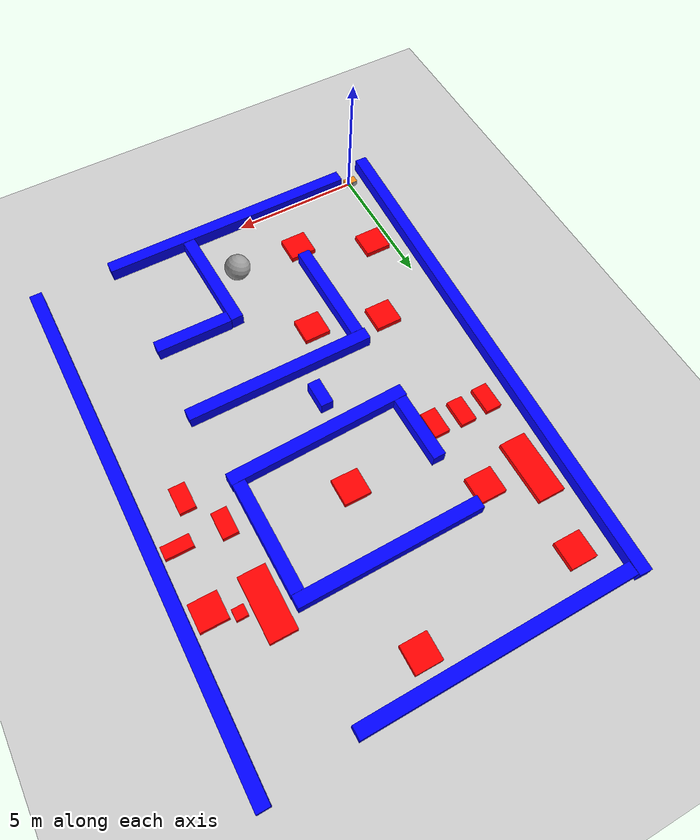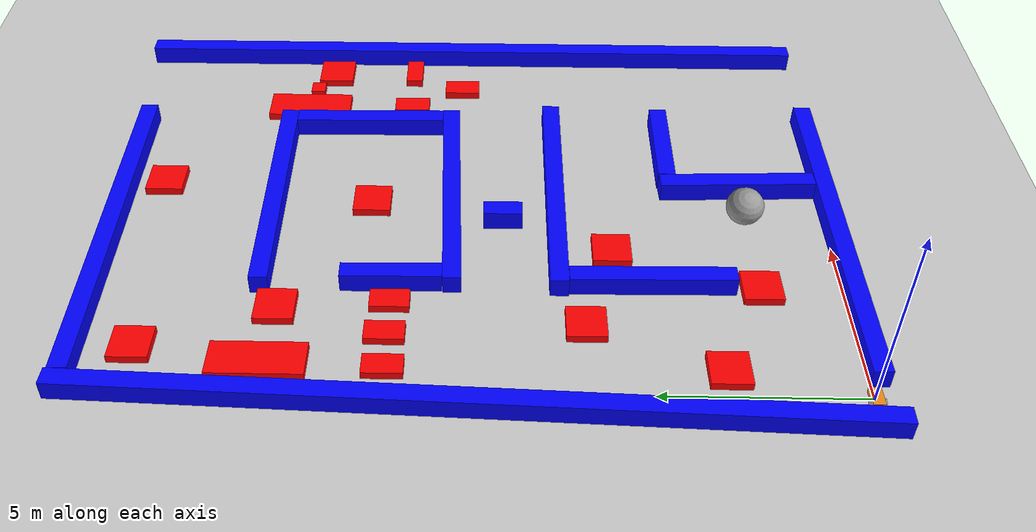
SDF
<sdf version="1.7">
 <world name="default">
  <light name="sun" type="directional">
   <pose>0 0 10 0 -0 0</pose>
   <diffuse>0.8 0.8 0.8 1</diffuse>
   <specular>0.2 0.2 0.2 1</specular>
   <attenuation>
    <range>1000</range>
    <constant>0.9</constant>
    <linear>0.01</linear>
    <quadratic>0.001</quadratic>
   </attenuation>
   <direction>-0.5 0.1 -0.9</direction>
   <spot><inner_angle>0</inner_angle><outer_angle>0</outer_angle><falloff>0</falloff></spot>
  </light>
  <model name="ground_plane">
   <static>1</static>
   <link name="link">
    <collision name="collision">
     <geometry><plane><normal>0 0 1</normal><size>100 100</size></plane></geometry>
     <surface>
      <contact><collide_bitmask>65535</collide_bitmask></contact>
      <friction><ode><mu>100</mu><mu2>50</mu2></ode></friction>
     </surface>
    </collision>
    <visual name="visual">
     <cast_shadows>0</cast_shadows>
     <geometry><plane><normal>0 0 1</normal><size>100 100</size></plane></geometry>
     <material>
      <script><uri>file://media/materials/scripts/gazebo.material</uri><name>Gazebo/Grey</name></script>
     </material>
    </visual>
   </link>
  </model>
  <gravity>0 0 -9.8</gravity>
  <magnetic_field>6e-06 2.3e-05 -4.2e-05</magnetic_field>
  <atmosphere type="adiabatic"/>
  <physics type="ode">
   <max_step_size>0.001</max_step_size>
   <real_time_factor>1</real_time_factor>
   <real_time_update_rate>1000</real_time_update_rate>
  </physics>
  <scene><ambient>0.4 0.4 0.4 1</ambient><background>0.7 0.7 0.7 1</background><shadows>1</shadows></scene>
  <spherical_coordinates>
   <surface_model>EARTH_WGS84</surface_model>
   <latitude_deg>0</latitude_deg>
   <longitude_deg>0</longitude_deg>
   <elevation>0</elevation>
   <heading_deg>0</heading_deg>
  </spherical_coordinates>
  <model name="blue__wall">
   <link name="link_0">
    <inertial>
     <mass>3.38479</mass>
     <inertia><ixx>51.2617</ixx><ixy>0</ixy><ixz>0</ixz><iyy>0.142515</iyy><iyz>0</iyz><izz>51.2469</izz></inertia>
    </inertial>
    <visual name="visual">
     <geometry><box><size>0.47589 19.6362 0.528001</size></box></geometry>
     <material>
      <lighting>1</lighting>
      <script><uri>file://media/materials/scripts/gazebo.material</uri><name>Gazebo/Grey</name></script>
      <shader type="pixel"><normal_map>__default__</normal_map></shader>
      <ambient>0 0 1 0</ambient>
      <diffuse>0.7 0.7 0.7 1</diffuse>
      <specular>0.01 0.01 0.01 1</specular>
      <emissive>0 0 0 1</emissive>
     </material>
    </visual>
    <collision name="collision">
     <geometry><box><size>0.47589 19.6362 0.528001</size></box></geometry>
     <surface>
      <friction>
       <ode><mu>1</mu><mu2>1</mu2><fdir1>0 0 0</fdir1><slip1>0</slip1><slip2>0</slip2></ode>
       <torsional>
        <coefficient>1</coefficient>
        <patch_radius>0</patch_radius>
        <surface_radius>0</surface_radius>
        <use_patch_radius>1</use_patch_radius>
        <ode><slip>0</slip></ode>
       </torsional>
      </friction>
      <bounce><restitution_coefficient>0</restitution_coefficient><threshold>1e+06</threshold></bounce>
      <contact>
       <collide_without_contact>0</collide_without_contact>
       <collide_without_contact_bitmask>1</collide_without_contact_bitmask>
       <collide_bitmask>1</collide_bitmask>
       <ode>
        <soft_cfm>0</soft_cfm>
        <soft_erp>0.2</soft_erp>
        <kp>1e+13</kp>
        <kd>1</kd>
        <max_vel>0.01</max_vel>
        <min_depth>0</min_depth>
       </ode>
       <bullet>
        <split_impulse>1</split_impulse>
        <split_impulse_penetration_threshold>-0.01</split_impulse_penetration_threshold>
        <soft_cfm>0</soft_cfm>
        <soft_erp>0.2</soft_erp>
        <kp>1e+13</kp>
        <kd>1</kd>
       </bullet>
      </contact>
     </surface>
    </collision>
   </link>
   <static>0</static>
   <pose>-0.4804 9.22676 0.263996 0 -1.8e-05 -0.038056</pose>
  </model>
  <model name="blue__wall_clone_clone_clone">
   <link name="link_0">
    <inertial>
     <mass>3.38479</mass>
     <inertia><ixx>51.2617</ixx><ixy>0</ixy><ixz>0</ixz><iyy>0.142515</iyy><iyz>0</iyz><izz>51.2469</izz></inertia>
    </inertial>
    <visual name="visual">
     <geometry><box><size>0.47589 10.1039 0.528001</size></box></geometry>
     <material>
      <lighting>1</lighting>
      <script><uri>file://media/materials/scripts/gazebo.material</uri><name>Gazebo/Grey</name></script>
      <shader type="pixel"><normal_map>__default__</normal_map></shader>
      <ambient>0 0 1 0</ambient>
      <diffuse>0.7 0.7 0.7 1</diffuse>
      <specular>0.01 0.01 0.01 1</specular>
      <emissive>0 0 0 1</emissive>
     </material>
    </visual>
    <collision name="collision">
     <geometry><box><size>0.47589 10.1039 0.528001</size></box></geometry>
     <surface>
      <friction>
       <ode><mu>1</mu><mu2>1</mu2><fdir1>0 0 0</fdir1><slip1>0</slip1><slip2>0</slip2></ode>
       <torsional>
        <coefficient>1</coefficient>
        <patch_radius>0</patch_radius>
        <surface_radius>0</surface_radius>
        <use_patch_radius>1</use_patch_radius>
        <ode><slip>0</slip></ode>
       </torsional>
      </friction>
      <bounce><restitution_coefficient>0</restitution_coefficient><threshold>1e+06</threshold></bounce>
      <contact>
       <collide_without_contact>0</collide_without_contact>
       <collide_without_contact_bitmask>1</collide_without_contact_bitmask>
       <collide_bitmask>1</collide_bitmask>
       <ode>
        <soft_cfm>0</soft_cfm>
        <soft_erp>0.2</soft_erp>
        <kp>1e+13</kp>
        <kd>1</kd>
        <max_vel>0.01</max_vel>
        <min_depth>0</min_depth>
       </ode>
       <bullet>
        <split_impulse>1</split_impulse>
        <split_impulse_penetration_threshold>-0.01</split_impulse_penetration_threshold>
        <soft_cfm>0</soft_cfm>
        <soft_erp>0.2</soft_erp>
        <kp>1e+13</kp>
        <kd>1</kd>
       </bullet>
      </contact>
     </surface>
    </collision>
   </link>
   <static>0</static>
   <pose>5.44581 -0.183339 0.264 0 -0 1.57294</pose>
  </model>
  <model name="blue__wall_clone_clone_clone_clone">
   <link name="link_0">
    <inertial>
     <mass>3.38479</mass>
     <inertia><ixx>51.2617</ixx><ixy>0</ixy><ixz>0</ixz><iyy>0.142515</iyy><iyz>0</iyz><izz>51.2469</izz></inertia>
    </inertial>
    <visual name="visual">
     <geometry><box><size>0.47589 10.1039 0.528001</size></box></geometry>
     <material>
      <lighting>1</lighting>
      <script><uri>file://media/materials/scripts/gazebo.material</uri><name>Gazebo/Grey</name></script>
      <shader type="pixel"><normal_map>__default__</normal_map></shader>
      <ambient>0 0 1 0</ambient>
      <diffuse>0.7 0.7 0.7 1</diffuse>
      <specular>0.01 0.01 0.01 1</specular>
      <emissive>0 0 0 1</emissive>
     </material>
    </visual>
    <collision name="collision">
     <geometry><box><size>0.47589 10.1039 0.528001</size></box></geometry>
     <surface>
      <friction>
       <ode><mu>1</mu><mu2>1</mu2><fdir1>0 0 0</fdir1><slip1>0</slip1><slip2>0</slip2></ode>
       <torsional>
        <coefficient>1</coefficient>
        <patch_radius>0</patch_radius>
        <surface_radius>0</surface_radius>
        <use_patch_radius>1</use_patch_radius>
        <ode><slip>0</slip></ode>
       </torsional>
      </friction>
      <bounce><restitution_coefficient>0</restitution_coefficient><threshold>1e+06</threshold></bounce>
      <contact>
       <collide_without_contact>0</collide_without_contact>
       <collide_without_contact_bitmask>1</collide_without_contact_bitmask>
       <collide_bitmask>1</collide_bitmask>
       <ode>
        <soft_cfm>0</soft_cfm>
        <soft_erp>0.2</soft_erp>
        <kp>1e+13</kp>
        <kd>1</kd>
        <max_vel>0.01</max_vel>
        <min_depth>0</min_depth>
       </ode>
       <bullet>
        <split_impulse>1</split_impulse>
        <split_impulse_penetration_threshold>-0.01</split_impulse_penetration_threshold>
        <soft_cfm>0</soft_cfm>
        <soft_erp>0.2</soft_erp>
        <kp>1e+13</kp>
        <kd>1</kd>
       </bullet>
      </contact>
     </surface>
    </collision>
   </link>
   <static>0</static>
   <pose>5.18293 18.7739 0.264 0 -0 1.58016</pose>
  </model>
  <model name="blue__wall_clone_clone_clone_clone_clone">
   <link name="link_0">
    <inertial>
     <mass>3.38479</mass>
     <inertia><ixx>51.2617</ixx><ixy>0</ixy><ixz>0</ixz><iyy>0.142515</iyy><iyz>0</iyz><izz>51.2469</izz></inertia>
    </inertial>
    <visual name="visual">
     <geometry><box><size>0.47589 6.9172 0.528001</size></box></geometry>
     <material>
      <lighting>1</lighting>
      <script><uri>file://media/materials/scripts/gazebo.material</uri><name>Gazebo/Grey</name></script>
      <shader type="pixel"><normal_map>__default__</normal_map></shader>
      <ambient>0 0 1 0</ambient>
      <diffuse>0.7 0.7 0.7 1</diffuse>
      <specular>0.01 0.01 0.01 1</specular>
      <emissive>0 0 0 1</emissive>
     </material>
    </visual>
    <collision name="collision">
     <geometry><box><size>0.47589 6.9172 0.528001</size></box></geometry>
     <surface>
      <friction>
       <ode><mu>1</mu><mu2>1</mu2><fdir1>0 0 0</fdir1><slip1>0</slip1><slip2>0</slip2></ode>
       <torsional>
        <coefficient>1</coefficient>
        <patch_radius>0</patch_radius>
        <surface_radius>0</surface_radius>
        <use_patch_radius>1</use_patch_radius>
        <ode><slip>0</slip></ode>
       </torsional>
      </friction>
      <bounce><restitution_coefficient>0</restitution_coefficient><threshold>1e+06</threshold></bounce>
      <contact>
       <collide_without_contact>0</collide_without_contact>
       <collide_without_contact_bitmask>1</collide_without_contact_bitmask>
       <collide_bitmask>1</collide_bitmask>
       <ode>
        <soft_cfm>0</soft_cfm>
        <soft_erp>0.2</soft_erp>
        <kp>1e+13</kp>
        <kd>1</kd>
        <max_vel>0.01</max_vel>
        <min_depth>0</min_depth>
       </ode>
       <bullet>
        <split_impulse>1</split_impulse>
        <split_impulse_penetration_threshold>-0.01</split_impulse_penetration_threshold>
        <soft_cfm>0</soft_cfm>
        <soft_erp>0.2</soft_erp>
        <kp>1e+13</kp>
        <kd>1</kd>
       </bullet>
      </contact>
     </surface>
    </collision>
   </link>
   <static>0</static>
   <pose>6.70418 9.89001 0.264 0 -0 1.60482</pose>
  </model>
  <model name="blue__wall_clone_clone_clone_clone_clone_clone">
   <link name="link_0">
    <inertial>
     <mass>3.38479</mass>
     <inertia><ixx>51.2617</ixx><ixy>0</ixy><ixz>0</ixz><iyy>0.142515</iyy><iyz>0</iyz><izz>51.2469</izz></inertia>
    </inertial>
    <visual name="visual">
     <geometry><box><size>0.47589 7.22384 0.528001</size></box></geometry>
     <material>
      <lighting>1</lighting>
      <script><uri>file://media/materials/scripts/gazebo.material</uri><name>Gazebo/Grey</name></script>
      <shader type="pixel"><normal_map>__default__</normal_map></shader>
      <ambient>0 0 1 0</ambient>
      <diffuse>0.7 0.7 0.7 1</diffuse>
      <specular>0.01 0.01 0.01 1</specular>
      <emissive>0 0 0 1</emissive>
     </material>
    </visual>
    <collision name="collision">
     <geometry><box><size>0.47589 7.22384 0.528001</size></box></geometry>
     <surface>
      <friction>
       <ode><mu>1</mu><mu2>1</mu2><fdir1>0 0 0</fdir1><slip1>0</slip1><slip2>0</slip2></ode>
       <torsional>
        <coefficient>1</coefficient>
        <patch_radius>0</patch_radius>
        <surface_radius>0</surface_radius>
        <use_patch_radius>1</use_patch_radius>
        <ode><slip>0</slip></ode>
       </torsional>
      </friction>
      <bounce><restitution_coefficient>0</restitution_coefficient><threshold>1e+06</threshold></bounce>
      <contact>
       <collide_without_contact>0</collide_without_contact>
       <collide_without_contact_bitmask>1</collide_without_contact_bitmask>
       <collide_bitmask>1</collide_bitmask>
       <ode>
        <soft_cfm>0</soft_cfm>
        <soft_erp>0.2</soft_erp>
        <kp>1e+13</kp>
        <kd>1</kd>
        <max_vel>0.01</max_vel>
        <min_depth>0</min_depth>
       </ode>
       <bullet>
        <split_impulse>1</split_impulse>
        <split_impulse_penetration_threshold>-0.01</split_impulse_penetration_threshold>
        <soft_cfm>0</soft_cfm>
        <soft_erp>0.2</soft_erp>
        <kp>1e+13</kp>
        <kd>1</kd>
       </bullet>
      </contact>
     </surface>
    </collision>
   </link>
   <static>0</static>
   <pose>6.79896 7.11272 0.264 0 -0 1.57503</pose>
  </model>
  <model name="blue__wall_clone_clone_clone_clone_clone_clone_clone">
   <link name="link_0">
    <inertial>
     <mass>3.38479</mass>
     <inertia><ixx>51.2617</ixx><ixy>0</ixy><ixz>0</ixz><iyy>0.142515</iyy><iyz>0</iyz><izz>51.2469</izz></inertia>
    </inertial>
    <visual name="visual">
     <geometry><box><size>0.47589 4.18247 0.528001</size></box></geometry>
     <material>
      <lighting>1</lighting>
      <script><uri>file://media/materials/scripts/gazebo.material</uri><name>Gazebo/Grey</name></script>
      <shader type="pixel"><normal_map>__default__</normal_map></shader>
      <ambient>0 0 1 0</ambient>
      <diffuse>0.7 0.7 0.7 1</diffuse>
      <specular>0.01 0.01 0.01 1</specular>
      <emissive>0 0 0 1</emissive>
     </material>
    </visual>
    <collision name="collision">
     <geometry><box><size>0.47589 4.18247 0.528001</size></box></geometry>
     <surface>
      <friction>
       <ode><mu>1</mu><mu2>1</mu2><fdir1>0 0 0</fdir1><slip1>0</slip1><slip2>0</slip2></ode>
       <torsional>
        <coefficient>1</coefficient>
        <patch_radius>0</patch_radius>
        <surface_radius>0</surface_radius>
        <use_patch_radius>1</use_patch_radius>
        <ode><slip>0</slip></ode>
       </torsional>
      </friction>
      <bounce><restitution_coefficient>0</restitution_coefficient><threshold>1e+06</threshold></bounce>
      <contact>
       <collide_without_contact>0</collide_without_contact>
       <collide_without_contact_bitmask>1</collide_without_contact_bitmask>
       <collide_bitmask>1</collide_bitmask>
       <ode>
        <soft_cfm>0</soft_cfm>
        <soft_erp>0.2</soft_erp>
        <kp>1e+13</kp>
        <kd>1</kd>
        <max_vel>0.01</max_vel>
        <min_depth>0</min_depth>
       </ode>
       <bullet>
        <split_impulse>1</split_impulse>
        <split_impulse_penetration_threshold>-0.01</split_impulse_penetration_threshold>
        <soft_cfm>0</soft_cfm>
        <soft_erp>0.2</soft_erp>
        <kp>1e+13</kp>
        <kd>1</kd>
       </bullet>
      </contact>
     </surface>
    </collision>
   </link>
   <static>0</static>
   <pose>3.50966 4.76575 0.264 0 0 -3.13011</pose>
  </model>
  <model name="blue__wall_clone">
   <link name="link_0">
    <inertial>
     <mass>3.38479</mass>
     <inertia><ixx>51.2617</ixx><ixy>0</ixy><ixz>0</ixz><iyy>0.142515</iyy><iyz>0</iyz><izz>51.2469</izz></inertia>
    </inertial>
    <visual name="visual">
     <geometry><box><size>0.47589 19.6362 0.528001</size></box></geometry>
     <material>
      <lighting>1</lighting>
      <script><uri>file://media/materials/scripts/gazebo.material</uri><name>Gazebo/Grey</name></script>
      <shader type="pixel"><normal_map>__default__</normal_map></shader>
      <ambient>0 0 1 0</ambient>
      <diffuse>0.7 0.7 0.7 1</diffuse>
      <specular>0.01 0.01 0.01 1</specular>
      <emissive>0 0 0 1</emissive>
     </material>
    </visual>
    <collision name="collision">
     <geometry><box><size>0.47589 19.6362 0.528001</size></box></geometry>
     <surface>
      <friction>
       <ode><mu>1</mu><mu2>1</mu2><fdir1>0 0 0</fdir1><slip1>0</slip1><slip2>0</slip2></ode>
       <torsional>
        <coefficient>1</coefficient>
        <patch_radius>0</patch_radius>
        <surface_radius>0</surface_radius>
        <use_patch_radius>1</use_patch_radius>
        <ode><slip>0</slip></ode>
       </torsional>
      </friction>
      <bounce><restitution_coefficient>0</restitution_coefficient><threshold>1e+06</threshold></bounce>
      <contact>
       <collide_without_contact>0</collide_without_contact>
       <collide_without_contact_bitmask>1</collide_without_contact_bitmask>
       <collide_bitmask>1</collide_bitmask>
       <ode>
        <soft_cfm>0</soft_cfm>
        <soft_erp>0.2</soft_erp>
        <kp>1e+13</kp>
        <kd>1</kd>
        <max_vel>0.01</max_vel>
        <min_depth>0</min_depth>
       </ode>
       <bullet>
        <split_impulse>1</split_impulse>
        <split_impulse_penetration_threshold>-0.01</split_impulse_penetration_threshold>
        <soft_cfm>0</soft_cfm>
        <soft_erp>0.2</soft_erp>
        <kp>1e+13</kp>
        <kd>1</kd>
       </bullet>
      </contact>
     </surface>
    </collision>
   </link>
   <static>0</static>
   <pose>13.4295 9.53036 0.264001 0 1e-06 0</pose>
  </model>
  <model name="blue__wall_clone_clone_clone_clone_clone_clone_clone_clone">
   <link name="link_0">
    <inertial>
     <mass>3.38479</mass>
     <inertia><ixx>51.2617</ixx><ixy>0</ixy><ixz>0</ixz><iyy>0.142515</iyy><iyz>0</iyz><izz>51.2469</izz></inertia>
    </inertial>
    <visual name="visual">
     <geometry><box><size>0.47589 4.18247 0.528001</size></box></geometry>
     <material>
      <lighting>1</lighting>
      <script><uri>file://media/materials/scripts/gazebo.material</uri><name>Gazebo/Grey</name></script>
      <shader type="pixel"><normal_map>__default__</normal_map></shader>
      <ambient>0 0 1 0</ambient>
      <diffuse>0.7 0.7 0.7 1</diffuse>
      <specular>0.01 0.01 0.01 1</specular>
      <emissive>0 0 0 1</emissive>
     </material>
    </visual>
    <collision name="collision">
     <geometry><box><size>0.47589 4.18247 0.528001</size></box></geometry>
     <surface>
      <friction>
       <ode><mu>1</mu><mu2>1</mu2><fdir1>0 0 0</fdir1><slip1>0</slip1><slip2>0</slip2></ode>
       <torsional>
        <coefficient>1</coefficient>
        <patch_radius>0</patch_radius>
        <surface_radius>0</surface_radius>
        <use_patch_radius>1</use_patch_radius>
        <ode><slip>0</slip></ode>
       </torsional>
      </friction>
      <bounce><restitution_coefficient>0</restitution_coefficient><threshold>1e+06</threshold></bounce>
      <contact>
       <collide_without_contact>0</collide_without_contact>
       <collide_without_contact_bitmask>1</collide_without_contact_bitmask>
       <collide_bitmask>1</collide_bitmask>
       <ode>
        <soft_cfm>0</soft_cfm>
        <soft_erp>0.2</soft_erp>
        <kp>1e+13</kp>
        <kd>1</kd>
        <max_vel>0.01</max_vel>
        <min_depth>0</min_depth>
       </ode>
       <bullet>
        <split_impulse>1</split_impulse>
        <split_impulse_penetration_threshold>-0.01</split_impulse_penetration_threshold>
        <soft_cfm>0</soft_cfm>
        <soft_erp>0.2</soft_erp>
        <kp>1e+13</kp>
        <kd>1</kd>
       </bullet>
      </contact>
     </surface>
    </collision>
   </link>
   <static>0</static>
   <pose>7.20045 2.16332 0.263994 -0 -1.1e-05 -3.10777</pose>
  </model>
  <model name="blue__wall_clone_clone_clone_clone_clone_clone_clone_clone_clone">
   <link name="link_0">
    <inertial>
     <mass>3.38479</mass>
     <inertia><ixx>51.2617</ixx><ixy>0</ixy><ixz>0</ixz><iyy>0.142515</iyy><iyz>0</iyz><izz>51.2469</izz></inertia>
    </inertial>
    <visual name="visual">
     <geometry><box><size>0.47589 2.55946 0.528001</size></box></geometry>
     <material>
      <lighting>1</lighting>
      <script><uri>file://media/materials/scripts/gazebo.material</uri><name>Gazebo/Grey</name></script>
      <shader type="pixel"><normal_map>__default__</normal_map></shader>
      <ambient>0 0 1 0</ambient>
      <diffuse>0.7 0.7 0.7 1</diffuse>
      <specular>0.01 0.01 0.01 1</specular>
      <emissive>0 0 0 1</emissive>
     </material>
    </visual>
    <collision name="collision">
     <geometry><box><size>0.47589 2.55946 0.528001</size></box></geometry>
     <surface>
      <friction>
       <ode><mu>1</mu><mu2>1</mu2><fdir1>0 0 0</fdir1><slip1>0</slip1><slip2>0</slip2></ode>
       <torsional>
        <coefficient>1</coefficient>
        <patch_radius>0</patch_radius>
        <surface_radius>0</surface_radius>
        <use_patch_radius>1</use_patch_radius>
        <ode><slip>0</slip></ode>
       </torsional>
      </friction>
      <bounce><restitution_coefficient>0</restitution_coefficient><threshold>1e+06</threshold></bounce>
      <contact>
       <collide_without_contact>0</collide_without_contact>
       <collide_without_contact_bitmask>1</collide_without_contact_bitmask>
       <collide_bitmask>1</collide_bitmask>
       <ode>
        <soft_cfm>0</soft_cfm>
        <soft_erp>0.2</soft_erp>
        <kp>1e+13</kp>
        <kd>1</kd>
        <max_vel>0.01</max_vel>
        <min_depth>0</min_depth>
       </ode>
       <bullet>
        <split_impulse>1</split_impulse>
        <split_impulse_penetration_threshold>-0.01</split_impulse_penetration_threshold>
        <soft_cfm>0</soft_cfm>
        <soft_erp>0.2</soft_erp>
        <kp>1e+13</kp>
        <kd>1</kd>
       </bullet>
      </contact>
     </surface>
    </collision>
   </link>
   <static>0</static>
   <pose>3.50586 11.3064 0.264 0 0 -3.12763</pose>
  </model>
  <model name="blue__wall_clone_clone_clone_clone_clone_clone_clone_clone_clone_0">
   <link name="link_0">
    <inertial>
     <mass>3.38479</mass>
     <inertia><ixx>51.2617</ixx><ixy>0</ixy><ixz>0</ixz><iyy>0.142515</iyy><iyz>0</iyz><izz>51.2469</izz></inertia>
    </inertial>
    <visual name="visual">
     <geometry><box><size>0.47589 4.18247 0.528001</size></box></geometry>
     <material>
      <lighting>1</lighting>
      <script><uri>file://media/materials/scripts/gazebo.material</uri><name>Gazebo/Grey</name></script>
      <shader type="pixel"><normal_map>__default__</normal_map></shader>
      <ambient>0 0 1 0</ambient>
      <diffuse>0.7 0.7 0.7 1</diffuse>
      <specular>0.01 0.01 0.01 1</specular>
      <emissive>0 0 0 1</emissive>
     </material>
    </visual>
    <collision name="collision">
     <geometry><box><size>0.47589 4.18247 0.528001</size></box></geometry>
     <surface>
      <friction>
       <ode><mu>1</mu><mu2>1</mu2><fdir1>0 0 0</fdir1><slip1>0</slip1><slip2>0</slip2></ode>
       <torsional>
        <coefficient>1</coefficient>
        <patch_radius>0</patch_radius>
        <surface_radius>0</surface_radius>
        <use_patch_radius>1</use_patch_radius>
        <ode><slip>0</slip></ode>
       </torsional>
      </friction>
      <bounce><restitution_coefficient>0</restitution_coefficient><threshold>1e+06</threshold></bounce>
      <contact>
       <collide_without_contact>0</collide_without_contact>
       <collide_without_contact_bitmask>1</collide_without_contact_bitmask>
       <collide_bitmask>1</collide_bitmask>
       <ode>
        <soft_cfm>0</soft_cfm>
        <soft_erp>0.2</soft_erp>
        <kp>1e+13</kp>
        <kd>1</kd>
        <max_vel>0.01</max_vel>
        <min_depth>0</min_depth>
       </ode>
       <bullet>
        <split_impulse>1</split_impulse>
        <split_impulse_penetration_threshold>-0.01</split_impulse_penetration_threshold>
        <soft_cfm>0</soft_cfm>
        <soft_erp>0.2</soft_erp>
        <kp>1e+13</kp>
        <kd>1</kd>
       </bullet>
      </contact>
     </surface>
    </collision>
   </link>
   <static>0</static>
   <pose>9.87082 12.3354 0.264 0 -0 -3.13011</pose>
  </model>
  <model name="blue__wall_clone_clone_clone_clone_clone_clone_clone_clone_clone_clone">
   <link name="link_0">
    <inertial>
     <mass>3.38479</mass>
     <inertia><ixx>51.2617</ixx><ixy>0</ixy><ixz>0</ixz><iyy>0.142515</iyy><iyz>0</iyz><izz>51.2469</izz></inertia>
    </inertial>
    <visual name="visual">
     <geometry><box><size>0.47589 2.9259 0.528001</size></box></geometry>
     <material>
      <lighting>1</lighting>
      <script><uri>file://media/materials/scripts/gazebo.material</uri><name>Gazebo/Grey</name></script>
      <shader type="pixel"><normal_map>__default__</normal_map></shader>
      <ambient>0 0 1 0</ambient>
      <diffuse>0.7 0.7 0.7 1</diffuse>
      <specular>0.01 0.01 0.01 1</specular>
      <emissive>0 0 0 1</emissive>
     </material>
    </visual>
    <collision name="collision">
     <geometry><box><size>0.47589 2.9259 0.528001</size></box></geometry>
     <surface>
      <friction>
       <ode><mu>1</mu><mu2>1</mu2><fdir1>0 0 0</fdir1><slip1>0</slip1><slip2>0</slip2></ode>
       <torsional>
        <coefficient>1</coefficient>
        <patch_radius>0</patch_radius>
        <surface_radius>0</surface_radius>
        <use_patch_radius>1</use_patch_radius>
        <ode><slip>0</slip></ode>
       </torsional>
      </friction>
      <bounce><restitution_coefficient>0</restitution_coefficient><threshold>1e+06</threshold></bounce>
      <contact>
       <collide_without_contact>0</collide_without_contact>
       <collide_without_contact_bitmask>1</collide_without_contact_bitmask>
       <collide_bitmask>1</collide_bitmask>
       <ode>
        <soft_cfm>0</soft_cfm>
        <soft_erp>0.2</soft_erp>
        <kp>1e+13</kp>
        <kd>1</kd>
        <max_vel>0.01</max_vel>
        <min_depth>0</min_depth>
       </ode>
       <bullet>
        <split_impulse>1</split_impulse>
        <split_impulse_penetration_threshold>-0.01</split_impulse_penetration_threshold>
        <soft_cfm>0</soft_cfm>
        <soft_erp>0.2</soft_erp>
        <kp>1e+13</kp>
        <kd>1</kd>
       </bullet>
      </contact>
     </surface>
    </collision>
   </link>
   <static>0</static>
   <pose>8.84694 4.03992 0.264001 0 -0 1.5659</pose>
  </model>
  <model name="blue__wall_clone_clone_clone_clone_clone_clone_clone_clone_clone_clone_0">
   <link name="link_0">
    <inertial>
     <mass>3.38479</mass>
     <inertia><ixx>51.2617</ixx><ixy>0</ixy><ixz>0</ixz><iyy>0.142515</iyy><iyz>0</iyz><izz>51.2469</izz></inertia>
    </inertial>
    <visual name="visual">
     <geometry><box><size>0.47589 1.03249 0.528001</size></box></geometry>
     <material>
      <lighting>1</lighting>
      <script><uri>file://media/materials/scripts/gazebo.material</uri><name>Gazebo/Grey</name></script>
      <shader type="pixel"><normal_map>__default__</normal_map></shader>
      <ambient>0 0 1 0</ambient>
      <diffuse>0.7 0.7 0.7 1</diffuse>
      <specular>0.01 0.01 0.01 1</specular>
      <emissive>0 0 0 1</emissive>
     </material>
    </visual>
    <collision name="collision">
     <geometry><box><size>0.47589 1.03249 0.528001</size></box></geometry>
     <surface>
      <friction>
       <ode><mu>1</mu><mu2>1</mu2><fdir1>0 0 0</fdir1><slip1>0</slip1><slip2>0</slip2></ode>
       <torsional>
        <coefficient>1</coefficient>
        <patch_radius>0</patch_radius>
        <surface_radius>0</surface_radius>
        <use_patch_radius>1</use_patch_radius>
        <ode><slip>0</slip></ode>
       </torsional>
      </friction>
      <bounce><restitution_coefficient>0</restitution_coefficient><threshold>1e+06</threshold></bounce>
      <contact>
       <collide_without_contact>0</collide_without_contact>
       <collide_without_contact_bitmask>1</collide_without_contact_bitmask>
       <collide_bitmask>1</collide_bitmask>
       <ode>
        <soft_cfm>0</soft_cfm>
        <soft_erp>0.2</soft_erp>
        <kp>1e+13</kp>
        <kd>1</kd>
        <max_vel>0.01</max_vel>
        <min_depth>0</min_depth>
       </ode>
       <bullet>
        <split_impulse>1</split_impulse>
        <split_impulse_penetration_threshold>-0.01</split_impulse_penetration_threshold>
        <soft_cfm>0</soft_cfm>
        <soft_erp>0.2</soft_erp>
        <kp>1e+13</kp>
        <kd>1</kd>
       </bullet>
      </contact>
     </surface>
    </collision>
   </link>
   <static>0</static>
   <pose>5.89774 8.51162 0.263999 -0 -8e-06 -3.12942</pose>
  </model>
  <model name="blue__wall_clone_clone_clone_clone_clone_clone_0">
   <link name="link_0">
    <inertial>
     <mass>3.38479</mass>
     <inertia><ixx>51.2617</ixx><ixy>0</ixy><ixz>0</ixz><iyy>0.142515</iyy><iyz>0</iyz><izz>51.2469</izz></inertia>
    </inertial>
    <visual name="visual">
     <geometry><box><size>0.47589 6.9172 0.528001</size></box></geometry>
     <material>
      <lighting>1</lighting>
      <script><uri>file://media/materials/scripts/gazebo.material</uri><name>Gazebo/Grey</name></script>
      <shader type="pixel"><normal_map>__default__</normal_map></shader>
      <ambient>0 0 1 0</ambient>
      <diffuse>0.7 0.7 0.7 1</diffuse>
      <specular>0.01 0.01 0.01 1</specular>
      <emissive>0 0 0 1</emissive>
     </material>
    </visual>
    <collision name="collision">
     <geometry><box><size>0.47589 6.9172 0.528001</size></box></geometry>
     <surface>
      <friction>
       <ode><mu>1</mu><mu2>1</mu2><fdir1>0 0 0</fdir1><slip1>0</slip1><slip2>0</slip2></ode>
       <torsional>
        <coefficient>1</coefficient>
        <patch_radius>0</patch_radius>
        <surface_radius>0</surface_radius>
        <use_patch_radius>1</use_patch_radius>
        <ode><slip>0</slip></ode>
       </torsional>
      </friction>
      <bounce><restitution_coefficient>0</restitution_coefficient><threshold>1e+06</threshold></bounce>
      <contact>
       <collide_without_contact>0</collide_without_contact>
       <collide_without_contact_bitmask>1</collide_without_contact_bitmask>
       <collide_bitmask>1</collide_bitmask>
       <ode>
        <soft_cfm>0</soft_cfm>
        <soft_erp>0.2</soft_erp>
        <kp>1e+13</kp>
        <kd>1</kd>
        <max_vel>0.01</max_vel>
        <min_depth>0</min_depth>
       </ode>
       <bullet>
        <split_impulse>1</split_impulse>
        <split_impulse_penetration_threshold>-0.01</split_impulse_penetration_threshold>
        <soft_cfm>0</soft_cfm>
        <soft_erp>0.2</soft_erp>
        <kp>1e+13</kp>
        <kd>1</kd>
       </bullet>
      </contact>
     </surface>
    </collision>
   </link>
   <static>0</static>
   <pose>6.61449 14.6269 0.264 0 -0 1.58316</pose>
  </model>
  <model name="red_mines">
   <link name="link_1">
    <inertial>
     <mass>1</mass>
     <inertia>
      <ixx>0.166667</ixx>
      <ixy>0</ixy>
      <ixz>0</ixz>
      <iyy>0.166667</iyy>
      <iyz>0</iyz>
      <izz>0.166667</izz>
     </inertia>
    </inertial>
    <visual name="visual">
     <geometry><box><size>1 2.35738 0.214149</size></box></geometry>
     <material>
      <lighting>1</lighting>
      <script><uri>file://media/materials/scripts/gazebo.material</uri><name>Gazebo/Grey</name></script>
      <shader type="pixel"><normal_map>__default__</normal_map></shader>
      <ambient>1 0 0 0</ambient>
      <diffuse>0.7 0.7 0.7 1</diffuse>
      <specular>0.01 0.01 0.01 1</specular>
      <emissive>0 0 0 1</emissive>
     </material>
    </visual>
    <collision name="collision">
     <geometry><box><size>1 2.35738 0.214149</size></box></geometry>
     <surface>
      <friction>
       <ode><mu>1</mu><mu2>1</mu2><fdir1>0 0 0</fdir1><slip1>0</slip1><slip2>0</slip2></ode>
       <torsional>
        <coefficient>1</coefficient>
        <patch_radius>0</patch_radius>
        <surface_radius>0</surface_radius>
        <use_patch_radius>1</use_patch_radius>
        <ode><slip>0</slip></ode>
       </torsional>
      </friction>
      <bounce><restitution_coefficient>0</restitution_coefficient><threshold>1e+06</threshold></bounce>
      <contact>
       <collide_without_contact>0</collide_without_contact>
       <collide_without_contact_bitmask>1</collide_without_contact_bitmask>
       <collide_bitmask>1</collide_bitmask>
       <ode>
        <soft_cfm>0</soft_cfm>
        <soft_erp>0.2</soft_erp>
        <kp>1e+13</kp>
        <kd>1</kd>
        <max_vel>0.01</max_vel>
        <min_depth>0</min_depth>
       </ode>
       <bullet>
        <split_impulse>1</split_impulse>
        <split_impulse_penetration_threshold>-0.01</split_impulse_penetration_threshold>
        <soft_cfm>0</soft_cfm>
        <soft_erp>0.2</soft_erp>
        <kp>1e+13</kp>
        <kd>1</kd>
       </bullet>
      </contact>
     </surface>
    </collision>
   </link>
   <static>0</static>
   <pose>10.8018 14.2028 0.10707 0 1e-05 -1e-06</pose>
  </model>
  <model name="red_mines_clone_clone">
   <link name="link_1">
    <inertial>
     <mass>1</mass>
     <inertia>
      <ixx>0.166667</ixx>
      <ixy>0</ixy>
      <ixz>0</ixz>
      <iyy>0.166667</iyy>
      <iyz>0</iyz>
      <izz>0.166667</izz>
     </inertia>
    </inertial>
    <visual name="visual">
     <geometry><box><size>1 1 0.214149</size></box></geometry>
     <material>
      <lighting>1</lighting>
      <script><uri>file://media/materials/scripts/gazebo.material</uri><name>Gazebo/Grey</name></script>
      <shader type="pixel"><normal_map>__default__</normal_map></shader>
      <ambient>1 0 0 0</ambient>
      <diffuse>0.7 0.7 0.7 1</diffuse>
      <specular>0.01 0.01 0.01 1</specular>
      <emissive>0 0 0 1</emissive>
     </material>
    </visual>
    <collision name="collision">
     <geometry><box><size>1 1 0.214149</size></box></geometry>
     <surface>
      <friction>
       <ode><mu>1</mu><mu2>1</mu2><fdir1>0 0 0</fdir1><slip1>0</slip1><slip2>0</slip2></ode>
       <torsional>
        <coefficient>1</coefficient>
        <patch_radius>0</patch_radius>
        <surface_radius>0</surface_radius>
        <use_patch_radius>1</use_patch_radius>
        <ode><slip>0</slip></ode>
       </torsional>
      </friction>
      <bounce><restitution_coefficient>0</restitution_coefficient><threshold>1e+06</threshold></bounce>
      <contact>
       <collide_without_contact>0</collide_without_contact>
       <collide_without_contact_bitmask>1</collide_without_contact_bitmask>
       <collide_bitmask>1</collide_bitmask>
       <ode>
        <soft_cfm>0</soft_cfm>
        <soft_erp>0.2</soft_erp>
        <kp>1e+13</kp>
        <kd>1</kd>
        <max_vel>0.01</max_vel>
        <min_depth>0</min_depth>
       </ode>
       <bullet>
        <split_impulse>1</split_impulse>
        <split_impulse_penetration_threshold>-0.01</split_impulse_penetration_threshold>
        <soft_cfm>0</soft_cfm>
        <soft_erp>0.2</soft_erp>
        <kp>1e+13</kp>
        <kd>1</kd>
       </bullet>
      </contact>
     </surface>
    </collision>
   </link>
   <static>0</static>
   <pose>4.76211 5.70404 0.107074 0 -0 0</pose>
  </model>
  <model name="red_mines_clone_clone_clone">
   <link name="link_1">
    <inertial>
     <mass>1</mass>
     <inertia>
      <ixx>0.166667</ixx>
      <ixy>0</ixy>
      <ixz>0</ixz>
      <iyy>0.166667</iyy>
      <iyz>0</iyz>
      <izz>0.166667</izz>
     </inertia>
    </inertial>
    <visual name="visual">
     <geometry><box><size>1 1 0.214149</size></box></geometry>
     <material>
      <lighting>1</lighting>
      <script><uri>file://media/materials/scripts/gazebo.material</uri><name>Gazebo/Grey</name></script>
      <shader type="pixel"><normal_map>__default__</normal_map></shader>
      <ambient>1 0 0 0</ambient>
      <diffuse>0.7 0.7 0.7 1</diffuse>
      <specular>0.01 0.01 0.01 1</specular>
      <emissive>0 0 0 1</emissive>
     </material>
    </visual>
    <collision name="collision">
     <geometry><box><size>1 1 0.214149</size></box></geometry>
     <surface>
      <friction>
       <ode><mu>1</mu><mu2>1</mu2><fdir1>0 0 0</fdir1><slip1>0</slip1><slip2>0</slip2></ode>
       <torsional>
        <coefficient>1</coefficient>
        <patch_radius>0</patch_radius>
        <surface_radius>0</surface_radius>
        <use_patch_radius>1</use_patch_radius>
        <ode><slip>0</slip></ode>
       </torsional>
      </friction>
      <bounce><restitution_coefficient>0</restitution_coefficient><threshold>1e+06</threshold></bounce>
      <contact>
       <collide_without_contact>0</collide_without_contact>
       <collide_without_contact_bitmask>1</collide_without_contact_bitmask>
       <collide_bitmask>1</collide_bitmask>
       <ode>
        <soft_cfm>0</soft_cfm>
        <soft_erp>0.2</soft_erp>
        <kp>1e+13</kp>
        <kd>1</kd>
        <max_vel>0.01</max_vel>
        <min_depth>0</min_depth>
       </ode>
       <bullet>
        <split_impulse>1</split_impulse>
        <split_impulse_penetration_threshold>-0.01</split_impulse_penetration_threshold>
        <soft_cfm>0</soft_cfm>
        <soft_erp>0.2</soft_erp>
        <kp>1e+13</kp>
        <kd>1</kd>
       </bullet>
      </contact>
     </surface>
    </collision>
   </link>
   <static>0</static>
   <pose>1.26581 17.3408 0.107074 0 -0 0</pose>
  </model>
  <model name="red_mines_clone_clone_0">
   <link name="link_1">
    <inertial>
     <mass>1</mass>
     <inertia>
      <ixx>0.166667</ixx>
      <ixy>0</ixy>
      <ixz>0</ixz>
      <iyy>0.166667</iyy>
      <iyz>0</iyz>
      <izz>0.166667</izz>
     </inertia>
    </inertial>
    <visual name="visual">
     <geometry><box><size>0.580738 1 0.214149</size></box></geometry>
     <material>
      <lighting>1</lighting>
      <script><uri>file://media/materials/scripts/gazebo.material</uri><name>Gazebo/Grey</name></script>
      <shader type="pixel"><normal_map>__default__</normal_map></shader>
      <ambient>1 0 0 0</ambient>
      <diffuse>0.7 0.7 0.7 1</diffuse>
      <specular>0.01 0.01 0.01 1</specular>
      <emissive>0 0 0 1</emissive>
     </material>
    </visual>
    <collision name="collision">
     <geometry><box><size>0.580738 1 0.214149</size></box></geometry>
     <surface>
      <friction>
       <ode><mu>1</mu><mu2>1</mu2><fdir1>0 0 0</fdir1><slip1>0</slip1><slip2>0</slip2></ode>
       <torsional>
        <coefficient>1</coefficient>
        <patch_radius>0</patch_radius>
        <surface_radius>0</surface_radius>
        <use_patch_radius>1</use_patch_radius>
        <ode><slip>0</slip></ode>
       </torsional>
      </friction>
      <bounce><restitution_coefficient>0</restitution_coefficient><threshold>1e+06</threshold></bounce>
      <contact>
       <collide_without_contact>0</collide_without_contact>
       <collide_without_contact_bitmask>1</collide_without_contact_bitmask>
       <collide_bitmask>1</collide_bitmask>
       <ode>
        <soft_cfm>0</soft_cfm>
        <soft_erp>0.2</soft_erp>
        <kp>1e+13</kp>
        <kd>1</kd>
        <max_vel>0.01</max_vel>
        <min_depth>0</min_depth>
       </ode>
       <bullet>
        <split_impulse>1</split_impulse>
        <split_impulse_penetration_threshold>-0.01</split_impulse_penetration_threshold>
        <soft_cfm>0</soft_cfm>
        <soft_erp>0.2</soft_erp>
        <kp>1e+13</kp>
        <kd>1</kd>
       </bullet>
      </contact>
     </surface>
    </collision>
   </link>
   <static>0</static>
   <pose>10.8801 11.1899 0.107074 0 -0 0</pose>
  </model>
  <model name="red_mines_clone_clone_0_clone">
   <link name="link_1">
    <inertial>
     <mass>1</mass>
     <inertia>
      <ixx>0.166667</ixx>
      <ixy>0</ixy>
      <ixz>0</ixz>
      <iyy>0.166667</iyy>
      <iyz>0</iyz>
      <izz>0.166667</izz>
     </inertia>
    </inertial>
    <visual name="visual">
     <geometry><box><size>1.02755 0.479522 0.214149</size></box></geometry>
     <material>
      <lighting>1</lighting>
      <script><uri>file://media/materials/scripts/gazebo.material</uri><name>Gazebo/Grey</name></script>
      <shader type="pixel"><normal_map>__default__</normal_map></shader>
      <ambient>1 0 0 0</ambient>
      <diffuse>0.7 0.7 0.7 1</diffuse>
      <specular>0.01 0.01 0.01 1</specular>
      <emissive>0 0 0 1</emissive>
     </material>
    </visual>
    <collision name="collision">
     <geometry><box><size>1.02755 0.479522 0.214149</size></box></geometry>
     <surface>
      <friction>
       <ode><mu>1</mu><mu2>1</mu2><fdir1>0 0 0</fdir1><slip1>0</slip1><slip2>0</slip2></ode>
       <torsional>
        <coefficient>1</coefficient>
        <patch_radius>0</patch_radius>
        <surface_radius>0</surface_radius>
        <use_patch_radius>1</use_patch_radius>
        <ode><slip>0</slip></ode>
       </torsional>
      </friction>
      <bounce><restitution_coefficient>0</restitution_coefficient><threshold>1e+06</threshold></bounce>
      <contact>
       <collide_without_contact>0</collide_without_contact>
       <collide_without_contact_bitmask>1</collide_without_contact_bitmask>
       <collide_bitmask>1</collide_bitmask>
       <ode>
        <soft_cfm>0</soft_cfm>
        <soft_erp>0.2</soft_erp>
        <kp>1e+13</kp>
        <kd>1</kd>
        <max_vel>0.01</max_vel>
        <min_depth>0</min_depth>
       </ode>
       <bullet>
        <split_impulse>1</split_impulse>
        <split_impulse_penetration_threshold>-0.01</split_impulse_penetration_threshold>
        <soft_cfm>0</soft_cfm>
        <soft_erp>0.2</soft_erp>
        <kp>1e+13</kp>
        <kd>1</kd>
       </bullet>
      </contact>
     </surface>
    </collision>
   </link>
   <static>0</static>
   <pose>12.5777 11.2031 0.107074 0 -0 0</pose>
  </model>
  <model name="red_mines_clone_clone_1">
   <link name="link_1">
    <inertial>
     <mass>1</mass>
     <inertia>
      <ixx>0.166667</ixx>
      <ixy>0</ixy>
      <ixz>0</ixz>
      <iyy>0.166667</iyy>
      <iyz>0</iyz>
      <izz>0.166667</izz>
     </inertia>
    </inertial>
    <visual name="visual">
     <geometry><box><size>1.02755 1 0.214149</size></box></geometry>
     <material>
      <lighting>1</lighting>
      <script><uri>file://media/materials/scripts/gazebo.material</uri><name>Gazebo/Grey</name></script>
      <shader type="pixel"><normal_map>__default__</normal_map></shader>
      <ambient>1 0 0 0</ambient>
      <diffuse>0.7 0.7 0.7 1</diffuse>
      <specular>0.01 0.01 0.01 1</specular>
      <emissive>0 0 0 1</emissive>
     </material>
    </visual>
    <collision name="collision">
     <geometry><box><size>1.02755 1 0.214149</size></box></geometry>
     <surface>
      <friction>
       <ode><mu>1</mu><mu2>1</mu2><fdir1>0 0 0</fdir1><slip1>0</slip1><slip2>0</slip2></ode>
       <torsional>
        <coefficient>1</coefficient>
        <patch_radius>0</patch_radius>
        <surface_radius>0</surface_radius>
        <use_patch_radius>1</use_patch_radius>
        <ode><slip>0</slip></ode>
       </torsional>
      </friction>
      <bounce><restitution_coefficient>0</restitution_coefficient><threshold>1e+06</threshold></bounce>
      <contact>
       <collide_without_contact>0</collide_without_contact>
       <collide_without_contact_bitmask>1</collide_without_contact_bitmask>
       <collide_bitmask>1</collide_bitmask>
       <ode>
        <soft_cfm>0</soft_cfm>
        <soft_erp>0.2</soft_erp>
        <kp>1e+13</kp>
        <kd>1</kd>
        <max_vel>0.01</max_vel>
        <min_depth>0</min_depth>
       </ode>
       <bullet>
        <split_impulse>1</split_impulse>
        <split_impulse_penetration_threshold>-0.01</split_impulse_penetration_threshold>
        <soft_cfm>0</soft_cfm>
        <soft_erp>0.2</soft_erp>
        <kp>1e+13</kp>
        <kd>1</kd>
       </bullet>
      </contact>
     </surface>
    </collision>
   </link>
   <static>0</static>
   <pose>12.5402 13.5814 0.107074 0 -0 0</pose>
  </model>
  <model name="red_mines_clone_clone_0_clone_0">
   <link name="link_1">
    <inertial>
     <mass>1</mass>
     <inertia>
      <ixx>0.166667</ixx>
      <ixy>0</ixy>
      <ixz>0</ixz>
      <iyy>0.166667</iyy>
      <iyz>0</iyz>
      <izz>0.166667</izz>
     </inertia>
    </inertial>
    <visual name="visual">
     <geometry><box><size>0.602905 1 0.214149</size></box></geometry>
     <material>
      <lighting>1</lighting>
      <script><uri>file://media/materials/scripts/gazebo.material</uri><name>Gazebo/Grey</name></script>
      <shader type="pixel"><normal_map>__default__</normal_map></shader>
      <ambient>1 0 0 0</ambient>
      <diffuse>0.7 0.7 0.7 1</diffuse>
      <specular>0.01 0.01 0.01 1</specular>
      <emissive>0 0 0 1</emissive>
     </material>
    </visual>
    <collision name="collision">
     <geometry><box><size>0.602905 1 0.214149</size></box></geometry>
     <surface>
      <friction>
       <ode><mu>1</mu><mu2>1</mu2><fdir1>0 0 0</fdir1><slip1>0</slip1><slip2>0</slip2></ode>
       <torsional>
        <coefficient>1</coefficient>
        <patch_radius>0</patch_radius>
        <surface_radius>0</surface_radius>
        <use_patch_radius>1</use_patch_radius>
        <ode><slip>0</slip></ode>
       </torsional>
      </friction>
      <bounce><restitution_coefficient>0</restitution_coefficient><threshold>1e+06</threshold></bounce>
      <contact>
       <collide_without_contact>0</collide_without_contact>
       <collide_without_contact_bitmask>1</collide_without_contact_bitmask>
       <collide_bitmask>1</collide_bitmask>
       <ode>
        <soft_cfm>0</soft_cfm>
        <soft_erp>0.2</soft_erp>
        <kp>1e+13</kp>
        <kd>1</kd>
        <max_vel>0.01</max_vel>
        <min_depth>0</min_depth>
       </ode>
       <bullet>
        <split_impulse>1</split_impulse>
        <split_impulse_penetration_threshold>-0.01</split_impulse_penetration_threshold>
        <soft_cfm>0</soft_cfm>
        <soft_erp>0.2</soft_erp>
        <kp>1e+13</kp>
        <kd>1</kd>
       </bullet>
      </contact>
     </surface>
    </collision>
   </link>
   <static>0</static>
   <pose>11.7691 9.73126 0.107074 0 -0 0</pose>
  </model>
  <model name="red_mines_clone_clone_0_clone_0_clone">
   <link name="link_1">
    <inertial>
     <mass>1</mass>
     <inertia>
      <ixx>0.166667</ixx>
      <ixy>0</ixy>
      <ixz>0</ixz>
      <iyy>0.166667</iyy>
      <iyz>0</iyz>
      <izz>0.166667</izz>
     </inertia>
    </inertial>
    <visual name="visual">
     <geometry><box><size>0.431002 0.405557 0.214149</size></box></geometry>
     <material>
      <lighting>1</lighting>
      <script><uri>file://media/materials/scripts/gazebo.material</uri><name>Gazebo/Grey</name></script>
      <shader type="pixel"><normal_map>__default__</normal_map></shader>
      <ambient>1 0 0 0</ambient>
      <diffuse>0.7 0.7 0.7 1</diffuse>
      <specular>0.01 0.01 0.01 1</specular>
      <emissive>0 0 0 1</emissive>
     </material>
    </visual>
    <collision name="collision">
     <geometry><box><size>0.431002 0.405557 0.214149</size></box></geometry>
     <surface>
      <friction>
       <ode><mu>1</mu><mu2>1</mu2><fdir1>0 0 0</fdir1><slip1>0</slip1><slip2>0</slip2></ode>
       <torsional>
        <coefficient>1</coefficient>
        <patch_radius>0</patch_radius>
        <surface_radius>0</surface_radius>
        <use_patch_radius>1</use_patch_radius>
        <ode><slip>0</slip></ode>
       </torsional>
      </friction>
      <bounce><restitution_coefficient>0</restitution_coefficient><threshold>1e+06</threshold></bounce>
      <contact>
       <collide_without_contact>0</collide_without_contact>
       <collide_without_contact_bitmask>1</collide_without_contact_bitmask>
       <collide_bitmask>1</collide_bitmask>
       <ode>
        <soft_cfm>0</soft_cfm>
        <soft_erp>0.2</soft_erp>
        <kp>1e+13</kp>
        <kd>1</kd>
        <max_vel>0.01</max_vel>
        <min_depth>0</min_depth>
       </ode>
       <bullet>
        <split_impulse>1</split_impulse>
        <split_impulse_penetration_threshold>-0.01</split_impulse_penetration_threshold>
        <soft_cfm>0</soft_cfm>
        <soft_erp>0.2</soft_erp>
        <kp>1e+13</kp>
        <kd>1</kd>
       </bullet>
      </contact>
     </surface>
    </collision>
   </link>
   <static>0</static>
   <pose>11.6855 14.0674 0.107074 0 -0 0</pose>
  </model>
  <model name="red_mines_clone_clone_clone_clone">
   <link name="link_1">
    <inertial>
     <mass>1</mass>
     <inertia>
      <ixx>0.166667</ixx>
      <ixy>0</ixy>
      <ixz>0</ixz>
      <iyy>0.166667</iyy>
      <iyz>0</iyz>
      <izz>0.166667</izz>
     </inertia>
    </inertial>
    <visual name="visual">
     <geometry><box><size>1 1 0.214149</size></box></geometry>
     <material>
      <lighting>1</lighting>
      <script><uri>file://media/materials/scripts/gazebo.material</uri><name>Gazebo/Grey</name></script>
      <shader type="pixel"><normal_map>__default__</normal_map></shader>
      <ambient>1 0 0 0</ambient>
      <diffuse>0.7 0.7 0.7 1</diffuse>
      <specular>0.01 0.01 0.01 1</specular>
      <emissive>0 0 0 1</emissive>
     </material>
    </visual>
    <collision name="collision">
     <geometry><box><size>1 1 0.214149</size></box></geometry>
     <surface>
      <friction>
       <ode><mu>1</mu><mu2>1</mu2><fdir1>0 0 0</fdir1><slip1>0</slip1><slip2>0</slip2></ode>
       <torsional>
        <coefficient>1</coefficient>
        <patch_radius>0</patch_radius>
        <surface_radius>0</surface_radius>
        <use_patch_radius>1</use_patch_radius>
        <ode><slip>0</slip></ode>
       </torsional>
      </friction>
      <bounce><restitution_coefficient>0</restitution_coefficient><threshold>1e+06</threshold></bounce>
      <contact>
       <collide_without_contact>0</collide_without_contact>
       <collide_without_contact_bitmask>1</collide_without_contact_bitmask>
       <collide_bitmask>1</collide_bitmask>
       <ode>
        <soft_cfm>0</soft_cfm>
        <soft_erp>0.2</soft_erp>
        <kp>1e+13</kp>
        <kd>1</kd>
        <max_vel>0.01</max_vel>
        <min_depth>0</min_depth>
       </ode>
       <bullet>
        <split_impulse>1</split_impulse>
        <split_impulse_penetration_threshold>-0.01</split_impulse_penetration_threshold>
        <soft_cfm>0</soft_cfm>
        <soft_erp>0.2</soft_erp>
        <kp>1e+13</kp>
        <kd>1</kd>
       </bullet>
      </contact>
     </surface>
    </collision>
   </link>
   <static>0</static>
   <pose>3.46309 2.04332 0.107074 0 -0 0</pose>
  </model>
  <model name="red_mines_clone_clone_clone_clone_0">
   <link name="link_1">
    <inertial>
     <mass>1</mass>
     <inertia>
      <ixx>0.166667</ixx>
      <ixy>0</ixy>
      <ixz>0</ixz>
      <iyy>0.166667</iyy>
      <iyz>0</iyz>
      <izz>0.166667</izz>
     </inertia>
    </inertial>
    <visual name="visual">
     <geometry><box><size>1 1 0.214149</size></box></geometry>
     <material>
      <lighting>1</lighting>
      <script><uri>file://media/materials/scripts/gazebo.material</uri><name>Gazebo/Grey</name></script>
      <shader type="pixel"><normal_map>__default__</normal_map></shader>
      <ambient>1 0 0 0</ambient>
      <diffuse>0.7 0.7 0.7 1</diffuse>
      <specular>0.01 0.01 0.01 1</specular>
      <emissive>0 0 0 1</emissive>
     </material>
    </visual>
    <collision name="collision">
     <geometry><box><size>1 1 0.214149</size></box></geometry>
     <surface>
      <friction>
       <ode><mu>1</mu><mu2>1</mu2><fdir1>0 0 0</fdir1><slip1>0</slip1><slip2>0</slip2></ode>
       <torsional>
        <coefficient>1</coefficient>
        <patch_radius>0</patch_radius>
        <surface_radius>0</surface_radius>
        <use_patch_radius>1</use_patch_radius>
        <ode><slip>0</slip></ode>
       </torsional>
      </friction>
      <bounce><restitution_coefficient>0</restitution_coefficient><threshold>1e+06</threshold></bounce>
      <contact>
       <collide_without_contact>0</collide_without_contact>
       <collide_without_contact_bitmask>1</collide_without_contact_bitmask>
       <collide_bitmask>1</collide_bitmask>
       <ode>
        <soft_cfm>0</soft_cfm>
        <soft_erp>0.2</soft_erp>
        <kp>1e+13</kp>
        <kd>1</kd>
        <max_vel>0.01</max_vel>
        <min_depth>0</min_depth>
       </ode>
       <bullet>
        <split_impulse>1</split_impulse>
        <split_impulse_penetration_threshold>-0.01</split_impulse_penetration_threshold>
        <soft_cfm>0</soft_cfm>
        <soft_erp>0.2</soft_erp>
        <kp>1e+13</kp>
        <kd>1</kd>
       </bullet>
      </contact>
     </surface>
    </collision>
   </link>
   <static>0</static>
   <pose>0.732991 3.2216 0.107074 0 -0 0</pose>
  </model>
  <model name="red_mines_clone_clone_clone_clone_1">
   <link name="link_1">
    <inertial>
     <mass>1</mass>
     <inertia>
      <ixx>0.166667</ixx>
      <ixy>0</ixy>
      <ixz>0</ixz>
      <iyy>0.166667</iyy>
      <iyz>0</iyz>
      <izz>0.166667</izz>
     </inertia>
    </inertial>
    <visual name="visual">
     <geometry><box><size>1 1 0.214149</size></box></geometry>
     <material>
      <lighting>1</lighting>
      <script><uri>file://media/materials/scripts/gazebo.material</uri><name>Gazebo/Grey</name></script>
      <shader type="pixel"><normal_map>__default__</normal_map></shader>
      <ambient>1 0 0 0</ambient>
      <diffuse>0.7 0.7 0.7 1</diffuse>
      <specular>0.01 0.01 0.01 1</specular>
      <emissive>0 0 0 1</emissive>
     </material>
    </visual>
    <collision name="collision">
     <geometry><box><size>1 1 0.214149</size></box></geometry>
     <surface>
      <friction>
       <ode><mu>1</mu><mu2>1</mu2><fdir1>0 0 0</fdir1><slip1>0</slip1><slip2>0</slip2></ode>
       <torsional>
        <coefficient>1</coefficient>
        <patch_radius>0</patch_radius>
        <surface_radius>0</surface_radius>
        <use_patch_radius>1</use_patch_radius>
        <ode><slip>0</slip></ode>
       </torsional>
      </friction>
      <bounce><restitution_coefficient>0</restitution_coefficient><threshold>1e+06</threshold></bounce>
      <contact>
       <collide_without_contact>0</collide_without_contact>
       <collide_without_contact_bitmask>1</collide_without_contact_bitmask>
       <collide_bitmask>1</collide_bitmask>
       <ode>
        <soft_cfm>0</soft_cfm>
        <soft_erp>0.2</soft_erp>
        <kp>1e+13</kp>
        <kd>1</kd>
        <max_vel>0.01</max_vel>
        <min_depth>0</min_depth>
       </ode>
       <bullet>
        <split_impulse>1</split_impulse>
        <split_impulse_penetration_threshold>-0.01</split_impulse_penetration_threshold>
        <soft_cfm>0</soft_cfm>
        <soft_erp>0.2</soft_erp>
        <kp>1e+13</kp>
        <kd>1</kd>
       </bullet>
      </contact>
     </surface>
    </collision>
   </link>
   <static>0</static>
   <pose>2.13669 6.48173 0.107074 0 -0 0</pose>
  </model>
  <model name="red_mines_clone_clone_clone_clone_3">
   <link name="link_1">
    <inertial>
     <mass>1</mass>
     <inertia>
      <ixx>0.166667</ixx>
      <ixy>0</ixy>
      <ixz>0</ixz>
      <iyy>0.166667</iyy>
      <iyz>0</iyz>
      <izz>0.166667</izz>
     </inertia>
    </inertial>
    <visual name="visual">
     <geometry><box><size>1 1 0.214149</size></box></geometry>
     <material>
      <lighting>1</lighting>
      <script><uri>file://media/materials/scripts/gazebo.material</uri><name>Gazebo/Grey</name></script>
      <shader type="pixel"><normal_map>__default__</normal_map></shader>
      <ambient>1 0 0 0</ambient>
      <diffuse>0.7 0.7 0.7 1</diffuse>
      <specular>0.01 0.01 0.01 1</specular>
      <emissive>0 0 0 1</emissive>
     </material>
    </visual>
    <collision name="collision">
     <geometry><box><size>1 1 0.214149</size></box></geometry>
     <surface>
      <friction>
       <ode><mu>1</mu><mu2>1</mu2><fdir1>0 0 0</fdir1><slip1>0</slip1><slip2>0</slip2></ode>
       <torsional>
        <coefficient>1</coefficient>
        <patch_radius>0</patch_radius>
        <surface_radius>0</surface_radius>
        <use_patch_radius>1</use_patch_radius>
        <ode><slip>0</slip></ode>
       </torsional>
      </friction>
      <bounce><restitution_coefficient>0</restitution_coefficient><threshold>1e+06</threshold></bounce>
      <contact>
       <collide_without_contact>0</collide_without_contact>
       <collide_without_contact_bitmask>1</collide_without_contact_bitmask>
       <collide_bitmask>1</collide_bitmask>
       <ode>
        <soft_cfm>0</soft_cfm>
        <soft_erp>0.2</soft_erp>
        <kp>1e+13</kp>
        <kd>1</kd>
        <max_vel>0.01</max_vel>
        <min_depth>0</min_depth>
       </ode>
       <bullet>
        <split_impulse>1</split_impulse>
        <split_impulse_penetration_threshold>-0.01</split_impulse_penetration_threshold>
        <soft_cfm>0</soft_cfm>
        <soft_erp>0.2</soft_erp>
        <kp>1e+13</kp>
        <kd>1</kd>
       </bullet>
      </contact>
     </surface>
    </collision>
   </link>
   <static>0</static>
   <pose>6.59498 12.0215 0.107074 0 -0 0</pose>
  </model>
  <model name="red_mines_clone_clone_clone_clone_5">
   <link name="link_1">
    <inertial>
     <mass>1</mass>
     <inertia>
      <ixx>0.166667</ixx>
      <ixy>0</ixy>
      <ixz>0</ixz>
      <iyy>0.166667</iyy>
      <iyz>0</iyz>
      <izz>0.166667</izz>
     </inertia>
    </inertial>
    <visual name="visual">
     <geometry><box><size>1 1 0.214149</size></box></geometry>
     <material>
      <lighting>1</lighting>
      <script><uri>file://media/materials/scripts/gazebo.material</uri><name>Gazebo/Grey</name></script>
      <shader type="pixel"><normal_map>__default__</normal_map></shader>
      <ambient>1 0 0 0</ambient>
      <diffuse>0.7 0.7 0.7 1</diffuse>
      <specular>0.01 0.01 0.01 1</specular>
      <emissive>0 0 0 1</emissive>
     </material>
    </visual>
    <collision name="collision">
     <geometry><box><size>1 1 0.214149</size></box></geometry>
     <surface>
      <friction>
       <ode><mu>1</mu><mu2>1</mu2><fdir1>0 0 0</fdir1><slip1>0</slip1><slip2>0</slip2></ode>
       <torsional>
        <coefficient>1</coefficient>
        <patch_radius>0</patch_radius>
        <surface_radius>0</surface_radius>
        <use_patch_radius>1</use_patch_radius>
        <ode><slip>0</slip></ode>
       </torsional>
      </friction>
      <bounce><restitution_coefficient>0</restitution_coefficient><threshold>1e+06</threshold></bounce>
      <contact>
       <collide_without_contact>0</collide_without_contact>
       <collide_without_contact_bitmask>1</collide_without_contact_bitmask>
       <collide_bitmask>1</collide_bitmask>
       <ode>
        <soft_cfm>0</soft_cfm>
        <soft_erp>0.2</soft_erp>
        <kp>1e+13</kp>
        <kd>1</kd>
        <max_vel>0.01</max_vel>
        <min_depth>0</min_depth>
       </ode>
       <bullet>
        <split_impulse>1</split_impulse>
        <split_impulse_penetration_threshold>-0.01</split_impulse_penetration_threshold>
        <soft_cfm>0</soft_cfm>
        <soft_erp>0.2</soft_erp>
        <kp>1e+13</kp>
        <kd>1</kd>
       </bullet>
      </contact>
     </surface>
    </collision>
   </link>
   <static>0</static>
   <pose>7.34995 17.7583 0.107074 0 -0 0</pose>
  </model>
  <model name="red_mines_clone_clone_0_clone_0_clone_0">
   <link name="link_1">
    <inertial>
     <mass>1</mass>
     <inertia>
      <ixx>0.166667</ixx>
      <ixy>0</ixy>
      <ixz>0</ixz>
      <iyy>0.166667</iyy>
      <iyz>0</iyz>
      <izz>0.166667</izz>
     </inertia>
    </inertial>
    <visual name="visual">
     <geometry><box><size>0.602904 1 0.214149</size></box></geometry>
     <material>
      <lighting>1</lighting>
      <script><uri>file://media/materials/scripts/gazebo.material</uri><name>Gazebo/Grey</name></script>
      <shader type="pixel"><normal_map>__default__</normal_map></shader>
      <ambient>1 0 0 0</ambient>
      <diffuse>0.7 0.7 0.7 1</diffuse>
      <specular>0.01 0.01 0.01 1</specular>
      <emissive>0 0 0 1</emissive>
     </material>
    </visual>
    <collision name="collision">
     <geometry><box><size>0.602904 1 0.214149</size></box></geometry>
     <surface>
      <friction>
       <ode><mu>1</mu><mu2>1</mu2><fdir1>0 0 0</fdir1><slip1>0</slip1><slip2>0</slip2></ode>
       <torsional>
        <coefficient>1</coefficient>
        <patch_radius>0</patch_radius>
        <surface_radius>0</surface_radius>
        <use_patch_radius>1</use_patch_radius>
        <ode><slip>0</slip></ode>
       </torsional>
      </friction>
      <bounce><restitution_coefficient>0</restitution_coefficient><threshold>1e+06</threshold></bounce>
      <contact>
       <collide_without_contact>0</collide_without_contact>
       <collide_without_contact_bitmask>1</collide_without_contact_bitmask>
       <collide_bitmask>1</collide_bitmask>
       <ode>
        <soft_cfm>0</soft_cfm>
        <soft_erp>0.2</soft_erp>
        <kp>1e+13</kp>
        <kd>1</kd>
        <max_vel>0.01</max_vel>
        <min_depth>0</min_depth>
       </ode>
       <bullet>
        <split_impulse>1</split_impulse>
        <split_impulse_penetration_threshold>-0.01</split_impulse_penetration_threshold>
        <soft_cfm>0</soft_cfm>
        <soft_erp>0.2</soft_erp>
        <kp>1e+13</kp>
        <kd>1</kd>
       </bullet>
      </contact>
     </surface>
    </collision>
   </link>
   <static>0</static>
   <pose>0.696929 11.3162 0.107074 0 -0 0</pose>
  </model>
  <model name="red_mines_clone">
   <link name="link_1">
    <inertial>
     <mass>1</mass>
     <inertia>
      <ixx>0.166667</ixx>
      <ixy>0</ixy>
      <ixz>0</ixz>
      <iyy>0.166667</iyy>
      <iyz>0</iyz>
      <izz>0.166667</izz>
     </inertia>
    </inertial>
    <visual name="visual">
     <geometry><box><size>1 2.35739 0.214149</size></box></geometry>
     <material>
      <lighting>1</lighting>
      <script><uri>file://media/materials/scripts/gazebo.material</uri><name>Gazebo/Grey</name></script>
      <shader type="pixel"><normal_map>__default__</normal_map></shader>
      <ambient>1 0 0 0</ambient>
      <diffuse>0.7 0.7 0.7 1</diffuse>
      <specular>0.01 0.01 0.01 1</specular>
      <emissive>0 0 0 1</emissive>
     </material>
    </visual>
    <collision name="collision">
     <geometry><box><size>1 2.35739 0.214149</size></box></geometry>
     <surface>
      <friction>
       <ode><mu>1</mu><mu2>1</mu2><fdir1>0 0 0</fdir1><slip1>0</slip1><slip2>0</slip2></ode>
       <torsional>
        <coefficient>1</coefficient>
        <patch_radius>0</patch_radius>
        <surface_radius>0</surface_radius>
        <use_patch_radius>1</use_patch_radius>
        <ode><slip>0</slip></ode>
       </torsional>
      </friction>
      <bounce><restitution_coefficient>0</restitution_coefficient><threshold>1e+06</threshold></bounce>
      <contact>
       <collide_without_contact>0</collide_without_contact>
       <collide_without_contact_bitmask>1</collide_without_contact_bitmask>
       <collide_bitmask>1</collide_bitmask>
       <ode>
        <soft_cfm>0</soft_cfm>
        <soft_erp>0.2</soft_erp>
        <kp>1e+13</kp>
        <kd>1</kd>
        <max_vel>0.01</max_vel>
        <min_depth>0</min_depth>
       </ode>
       <bullet>
        <split_impulse>1</split_impulse>
        <split_impulse_penetration_threshold>-0.01</split_impulse_penetration_threshold>
        <soft_cfm>0</soft_cfm>
        <soft_erp>0.2</soft_erp>
        <kp>1e+13</kp>
        <kd>1</kd>
       </bullet>
      </contact>
     </surface>
    </collision>
   </link>
   <static>0</static>
   <pose>0.821955 14.2828 0.10707 0 1e-05 -1e-06</pose>
  </model>
  <model name="red_mines_clone_clone_1_clone">
   <link name="link_1">
    <inertial>
     <mass>1</mass>
     <inertia>
      <ixx>0.166667</ixx>
      <ixy>0</ixy>
      <ixz>0</ixz>
      <iyy>0.166667</iyy>
      <iyz>0</iyz>
      <izz>0.166667</izz>
     </inertia>
    </inertial>
    <visual name="visual">
     <geometry><box><size>1.02755 1 0.214149</size></box></geometry>
     <material>
      <lighting>1</lighting>
      <script><uri>file://media/materials/scripts/gazebo.material</uri><name>Gazebo/Grey</name></script>
      <shader type="pixel"><normal_map>__default__</normal_map></shader>
      <ambient>1 0 0 0</ambient>
      <diffuse>0.7 0.7 0.7 1</diffuse>
      <specular>0.01 0.01 0.01 1</specular>
      <emissive>0 0 0 1</emissive>
     </material>
    </visual>
    <collision name="collision">
     <geometry><box><size>1.02755 1 0.214149</size></box></geometry>
     <surface>
      <friction>
       <ode><mu>1</mu><mu2>1</mu2><fdir1>0 0 0</fdir1><slip1>0</slip1><slip2>0</slip2></ode>
       <torsional>
        <coefficient>1</coefficient>
        <patch_radius>0</patch_radius>
        <surface_radius>0</surface_radius>
        <use_patch_radius>1</use_patch_radius>
        <ode><slip>0</slip></ode>
       </torsional>
      </friction>
      <bounce><restitution_coefficient>0</restitution_coefficient><threshold>1e+06</threshold></bounce>
      <contact>
       <collide_without_contact>0</collide_without_contact>
       <collide_without_contact_bitmask>1</collide_without_contact_bitmask>
       <collide_bitmask>1</collide_bitmask>
       <ode>
        <soft_cfm>0</soft_cfm>
        <soft_erp>0.2</soft_erp>
        <kp>1e+13</kp>
        <kd>1</kd>
        <max_vel>0.01</max_vel>
        <min_depth>0</min_depth>
       </ode>
       <bullet>
        <split_impulse>1</split_impulse>
        <split_impulse_penetration_threshold>-0.01</split_impulse_penetration_threshold>
        <soft_cfm>0</soft_cfm>
        <soft_erp>0.2</soft_erp>
        <kp>1e+13</kp>
        <kd>1</kd>
       </bullet>
      </contact>
     </surface>
    </collision>
   </link>
   <static>0</static>
   <pose>2.58053 14.0961 0.107074 0 -0 0</pose>
  </model>
  <model name="red_mines_clone_clone_0_clone_0_clone_1">
   <link name="link_1">
    <inertial>
     <mass>1</mass>
     <inertia>
      <ixx>0.166667</ixx>
      <ixy>0</ixy>
      <ixz>0</ixz>
      <iyy>0.166667</iyy>
      <iyz>0</iyz>
      <izz>0.166667</izz>
     </inertia>
    </inertial>
    <visual name="visual">
     <geometry><box><size>0.602904 1 0.214149</size></box></geometry>
     <material>
      <lighting>1</lighting>
      <script><uri>file://media/materials/scripts/gazebo.material</uri><name>Gazebo/Grey</name></script>
      <shader type="pixel"><normal_map>__default__</normal_map></shader>
      <ambient>1 0 0 0</ambient>
      <diffuse>0.7 0.7 0.7 1</diffuse>
      <specular>0.01 0.01 0.01 1</specular>
      <emissive>0 0 0 1</emissive>
     </material>
    </visual>
    <collision name="collision">
     <geometry><box><size>0.602904 1 0.214149</size></box></geometry>
     <surface>
      <friction>
       <ode><mu>1</mu><mu2>1</mu2><fdir1>0 0 0</fdir1><slip1>0</slip1><slip2>0</slip2></ode>
       <torsional>
        <coefficient>1</coefficient>
        <patch_radius>0</patch_radius>
        <surface_radius>0</surface_radius>
        <use_patch_radius>1</use_patch_radius>
        <ode><slip>0</slip></ode>
       </torsional>
      </friction>
      <bounce><restitution_coefficient>0</restitution_coefficient><threshold>1e+06</threshold></bounce>
      <contact>
       <collide_without_contact>0</collide_without_contact>
       <collide_without_contact_bitmask>1</collide_without_contact_bitmask>
       <collide_bitmask>1</collide_bitmask>
       <ode>
        <soft_cfm>0</soft_cfm>
        <soft_erp>0.2</soft_erp>
        <kp>1e+13</kp>
        <kd>1</kd>
        <max_vel>0.01</max_vel>
        <min_depth>0</min_depth>
       </ode>
       <bullet>
        <split_impulse>1</split_impulse>
        <split_impulse_penetration_threshold>-0.01</split_impulse_penetration_threshold>
        <soft_cfm>0</soft_cfm>
        <soft_erp>0.2</soft_erp>
        <kp>1e+13</kp>
        <kd>1</kd>
       </bullet>
      </contact>
     </surface>
    </collision>
   </link>
   <static>0</static>
   <pose>1.76325 11.3508 0.107074 0 -0 0</pose>
  </model>
  <model name="red_mines_clone_clone_0_clone_0_clone_2">
   <link name="link_1">
    <inertial>
     <mass>1</mass>
     <inertia>
      <ixx>0.166667</ixx>
      <ixy>0</ixy>
      <ixz>0</ixz>
      <iyy>0.166667</iyy>
      <iyz>0</iyz>
      <izz>0.166667</izz>
     </inertia>
    </inertial>
    <visual name="visual">
     <geometry><box><size>0.602904 1 0.214149</size></box></geometry>
     <material>
      <lighting>1</lighting>
      <script><uri>file://media/materials/scripts/gazebo.material</uri><name>Gazebo/Grey</name></script>
      <shader type="pixel"><normal_map>__default__</normal_map></shader>
      <ambient>1 0 0 0</ambient>
      <diffuse>0.7 0.7 0.7 1</diffuse>
      <specular>0.01 0.01 0.01 1</specular>
      <emissive>0 0 0 1</emissive>
     </material>
    </visual>
    <collision name="collision">
     <geometry><box><size>0.602904 1 0.214149</size></box></geometry>
     <surface>
      <friction>
       <ode><mu>1</mu><mu2>1</mu2><fdir1>0 0 0</fdir1><slip1>0</slip1><slip2>0</slip2></ode>
       <torsional>
        <coefficient>1</coefficient>
        <patch_radius>0</patch_radius>
        <surface_radius>0</surface_radius>
        <use_patch_radius>1</use_patch_radius>
        <ode><slip>0</slip></ode>
       </torsional>
      </friction>
      <bounce><restitution_coefficient>0</restitution_coefficient><threshold>1e+06</threshold></bounce>
      <contact>
       <collide_without_contact>0</collide_without_contact>
       <collide_without_contact_bitmask>1</collide_without_contact_bitmask>
       <collide_bitmask>1</collide_bitmask>
       <ode>
        <soft_cfm>0</soft_cfm>
        <soft_erp>0.2</soft_erp>
        <kp>1e+13</kp>
        <kd>1</kd>
        <max_vel>0.01</max_vel>
        <min_depth>0</min_depth>
       </ode>
       <bullet>
        <split_impulse>1</split_impulse>
        <split_impulse_penetration_threshold>-0.01</split_impulse_penetration_threshold>
        <soft_cfm>0</soft_cfm>
        <soft_erp>0.2</soft_erp>
        <kp>1e+13</kp>
        <kd>1</kd>
       </bullet>
      </contact>
     </surface>
    </collision>
   </link>
   <static>0</static>
   <pose>2.83463 11.2991 0.107074 0 -0 0</pose>
  </model>
  <model name="robot_car">
   <link name="base_link">
    <inertial>
     <mass>10</mass>
     <inertia>
      <ixx>0.09375</ixx>
      <ixy>0</ixy>
      <ixz>0</ixz>
      <iyy>0.227083</iyy>
      <iyz>0</iyz>
      <izz>0.227083</izz>
     </inertia>
    </inertial>
    <collision name="base_link_fixed_joint_lump__collision_collision">
     <geometry><box><size>0.5 0.3 0.15</size></box></geometry>
    </collision>
    <collision name="base_link_fixed_joint_lump__caster_collision_collision_1">
     <pose>0.19625 0 -0.075 0 -0 0</pose>
     <geometry><sphere><radius>0.05375</radius></sphere></geometry>
    </collision>
    <visual name="base_link_visual_visual">
     <geometry><box><size>0.5 0.3 0.15</size></box></geometry>
     <material>
      <script><name>Gazebo/Orange</name><uri>file://media/materials/scripts/gazebo.material</uri></script>
     </material>
    </visual>
    <visual name="base_link_fixed_joint_lump__caster_visual_visual_1">
     <pose>0.19625 0 -0.075 0 -0 0</pose>
     <geometry><sphere><radius>0.05375</radius></sphere></geometry>
    </visual>
   </link>
   <joint name="left_wheel_hinge" type="revolute">
    <pose relative_to="base_link">-0.125 0.165 -0.02125 0 -0 0</pose>
    <parent>base_link</parent>
    <child>left_wheel</child>
    <axis>
     <xyz>0 1 0</xyz>
     <limit><effort>100</effort><velocity>100</velocity><lower>-1e+16</lower><upper>1e+16</upper></limit>
     <dynamics><spring_reference>0</spring_reference><spring_stiffness>0</spring_stiffness></dynamics>
    </axis>
   </joint>
   <link name="left_wheel">
    <pose relative_to="left_wheel_hinge">0 0 0 0 -0 0</pose>
    <inertial>
     <pose>0 0 0 -0 1.5707 1.5707</pose>
     <mass>3</mass>
     <inertia>
      <ixx>0.00889219</ixx>
      <ixy>0</ixy>
      <ixz>0</ixz>
      <iyy>0.00889219</iyy>
      <iyz>0</iyz>
      <izz>0.0173344</izz>
     </inertia>
    </inertial>
    <collision name="left_wheel_fixed_joint_lump__collision_collision">
     <pose>0 0 0 1.57089 1.57079 -3.14159</pose>
     <geometry><cylinder><length>0.03</length><radius>0.1075</radius></cylinder></geometry>
    </collision>
    <visual name="left_wheel_visual_visual">
     <pose>0 0 0 1.57089 1.57079 -3.14159</pose>
     <geometry><cylinder><length>0.03</length><radius>0.1075</radius></cylinder></geometry>
    </visual>
   </link>
   <joint name="right_wheel_hinge" type="revolute">
    <pose relative_to="base_link">-0.125 -0.165 -0.02125 0 -0 0</pose>
    <parent>base_link</parent>
    <child>right_wheel</child>
    <axis>
     <xyz>0 1 0</xyz>
     <limit><effort>100</effort><velocity>100</velocity><lower>-1e+16</lower><upper>1e+16</upper></limit>
     <dynamics><spring_reference>0</spring_reference><spring_stiffness>0</spring_stiffness></dynamics>
    </axis>
   </joint>
   <link name="right_wheel">
    <pose relative_to="right_wheel_hinge">0 0 0 0 -0 0</pose>
    <inertial>
     <pose>0 0 0 -0 1.5707 1.5707</pose>
     <mass>3</mass>
     <inertia>
      <ixx>0.00889219</ixx>
      <ixy>0</ixy>
      <ixz>0</ixz>
      <iyy>0.00889219</iyy>
      <iyz>0</iyz>
      <izz>0.0173344</izz>
     </inertia>
    </inertial>
    <collision name="right_wheel_fixed_joint_lump__collision_collision">
     <pose>0 0 0 1.57089 1.57079 -3.14159</pose>
     <geometry><cylinder><length>0.03</length><radius>0.1075</radius></cylinder></geometry>
    </collision>
    <visual name="right_wheel_visual_visual">
     <pose>0 0 0 1.57089 1.57079 -3.14159</pose>
     <geometry><cylinder><length>0.03</length><radius>0.1075</radius></cylinder></geometry>
    </visual>
   </link>
   <static>0</static>
   <plugin name="differential_drive_controller" filename="libgazebo_ros_diff_drive.so">
    <alwaysOn>1</alwaysOn>
    <updateRate>20</updateRate>
    <leftJoint>left_wheel_hinge</leftJoint>
    <rightJoint>right_wheel_hinge</rightJoint>
    <wheelSeparation>0.3576</wheelSeparation>
    <wheelDiameter>0.215</wheelDiameter>
    <wheelTorque>10</wheelTorque>
    <commandTopic>cmd_vel</commandTopic>
    <odometryTopic>odom</odometryTopic>
    <odometryFrame>odom_link</odometryFrame>
    <robotBaseFrame>base_link</robotBaseFrame>
    <legacyMode>0</legacyMode>
    <robotNamespace>/</robotNamespace>
   </plugin>
   <pose>-0.041365 0.001847 0.128748 -0 -1.1e-05 0.002046</pose>
  </model>
  <model name="unit_sphere">
   <pose>6.1207 2.1145 0.5 0.103836 -0.379273 0.006341</pose>
   <link name="link">
    <inertial>
     <mass>1</mass>
     <inertia><ixx>0.1</ixx><ixy>0</ixy><ixz>0</ixz><iyy>0.1</iyy><iyz>0</iyz><izz>0.1</izz></inertia>
    </inertial>
    <collision name="collision"><geometry><sphere><radius>0.5</radius></sphere></geometry></collision>
    <visual name="visual">
     <geometry><sphere><radius>0.5</radius></sphere></geometry>
     <material>
      <script><name>Gazebo/Grey</name><uri>file://media/materials/scripts/gazebo.material</uri></script>
     </material>
    </visual>
   </link>
  </model>
 </world>
</sdf>
